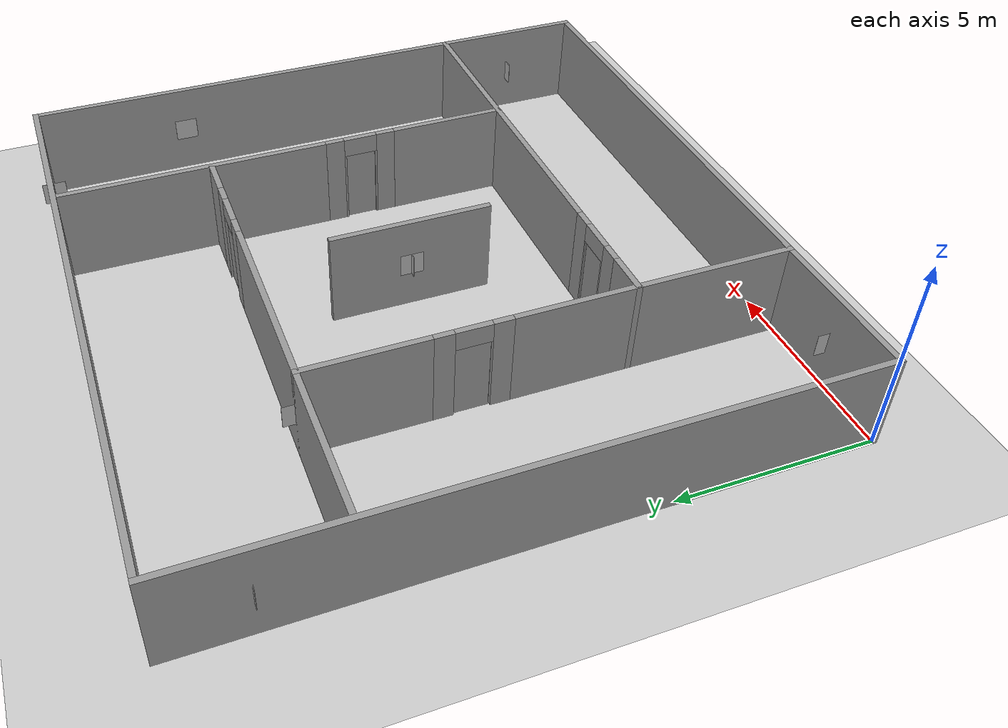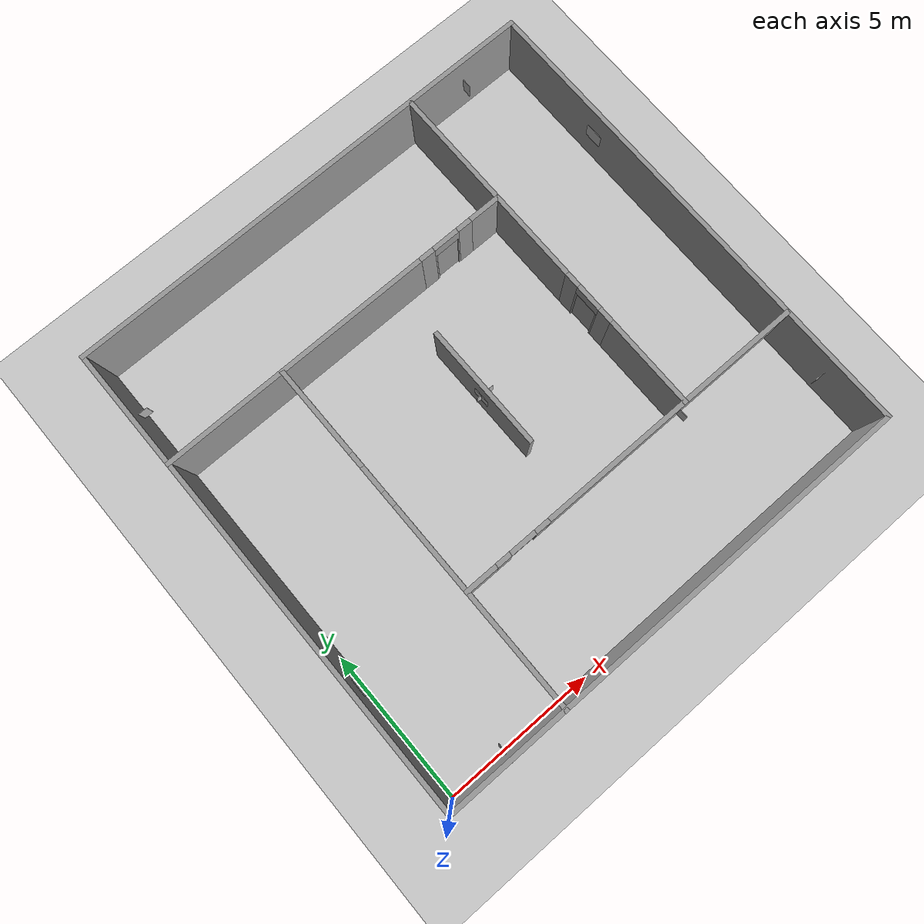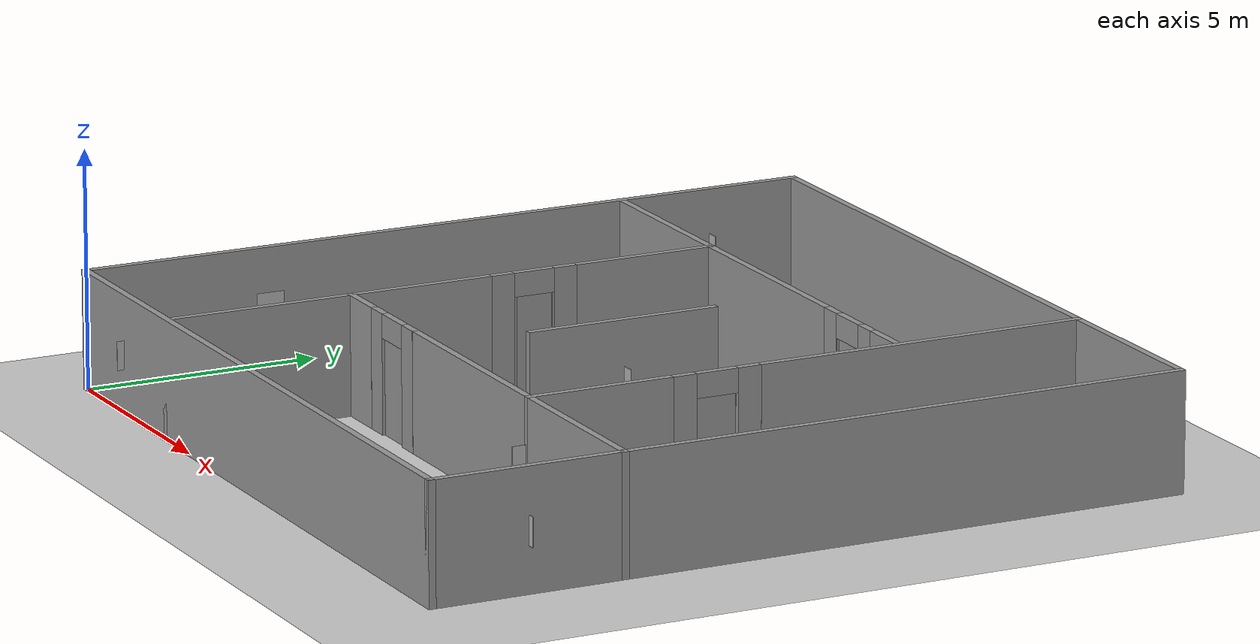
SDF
<sdf version="1.7">
 <world name="default">
  <light name="sun" type="directional">
   <pose>0 0 10 0 -0 0</pose>
   <diffuse>0.8 0.8 0.8 1</diffuse>
   <specular>0.2 0.2 0.2 1</specular>
   <attenuation>
    <range>1000</range>
    <constant>0.9</constant>
    <linear>0.01</linear>
    <quadratic>0.001</quadratic>
   </attenuation>
   <direction>-0.5 0.1 -0.9</direction>
   <spot><inner_angle>0</inner_angle><outer_angle>0</outer_angle><falloff>0</falloff></spot>
  </light>
  <model name="ground_plane">
   <static>1</static>
   <link name="link">
    <collision name="collision">
     <geometry><plane><normal>0 0 1</normal><size>100 100</size></plane></geometry>
     <surface><friction><ode><mu>100</mu><mu2>50</mu2></ode></friction></surface>
    </collision>
    <visual name="visual">
     <cast_shadows>0</cast_shadows>
     <geometry><plane><normal>0 0 1</normal><size>100 100</size></plane></geometry>
     <material>
      <script><uri>file://media/materials/scripts/gazebo.material</uri><name>Gazebo/Grey</name></script>
     </material>
    </visual>
   </link>
  </model>
  <gravity>0 0 -9.8</gravity>
  <magnetic_field>6e-06 2.3e-05 -4.2e-05</magnetic_field>
  <atmosphere type="adiabatic"/>
  <plugin name="ros_interface_plugin" filename="librotors_gazebo_ros_interface_plugin.so"/>
  <physics type="ode">
   <max_step_size>0.001</max_step_size>
   <real_time_factor>1</real_time_factor>
   <real_time_update_rate>1000</real_time_update_rate>
  </physics>
  <scene><ambient>0.4 0.4 0.4 1</ambient><background>0.7 0.7 0.7 1</background><shadows>1</shadows></scene>
  <spherical_coordinates>
   <surface_model>EARTH_WGS84</surface_model>
   <latitude_deg>0</latitude_deg>
   <longitude_deg>0</longitude_deg>
   <elevation>0</elevation>
   <heading_deg>0</heading_deg>
  </spherical_coordinates>
  <model name="room1">
   <pose>8 8 0 0 -0 0</pose>
   <link name="Wall_1">
    <collision name="Wall_1_Collision">
     <geometry><box><size>16.15 0.15 2.5</size></box></geometry>
     <pose>0 0 1.25 0 -0 0</pose>
    </collision>
    <visual name="Wall_1_Visual">
     <pose>0 0 1.25 0 -0 0</pose>
     <geometry><box><size>16.15 0.15 2.5</size></box></geometry>
     <material>
      <script><uri>file://media/materials/scripts/gazebo.material</uri><name>Gazebo/Grey</name></script>
      <ambient>1 1 1 1</ambient>
     </material>
     <meta><layer>0</layer></meta>
    </visual>
    <pose>0 -8 0 0 -0 0</pose>
   </link>
   <link name="Wall_11">
    <pose>-2 4 0 0 -0 0</pose>
    <visual name="Wall_11_Visual_0">
     <pose>-1.5125 0 1.25 0 -0 0</pose>
     <geometry><box><size>9.125 0.15 2.5</size></box></geometry>
     <material>
      <script><uri>file://media/materials/scripts/gazebo.material</uri><name>Gazebo/Grey</name></script>
      <ambient>1 1 1 1</ambient>
     </material>
     <meta><layer>0</layer></meta>
    </visual>
    <collision name="Wall_11_Collision_0">
     <geometry><box><size>9.125 0.15 2.5</size></box></geometry>
     <pose>-1.5125 0 1.25 0 -0 0</pose>
    </collision>
    <visual name="Wall_11_Visual_1">
     <pose>5.5125 0 1.25 0 -0 0</pose>
     <geometry><box><size>1.125 0.15 2.5</size></box></geometry>
     <material>
      <script><uri>file://media/materials/scripts/gazebo.material</uri><name>Gazebo/Grey</name></script>
      <ambient>1 1 1 1</ambient>
     </material>
     <meta><layer>0</layer></meta>
    </visual>
    <collision name="Wall_11_Collision_1">
     <geometry><box><size>1.125 0.15 2.5</size></box></geometry>
     <pose>5.5125 0 1.25 0 -0 0</pose>
    </collision>
   </link>
   <link name="Wall_13">
    <pose>4 2 0 0 -0 -1.5708</pose>
    <visual name="Wall_13_Visual_0">
     <pose>-2.5125 0 1.25 0 -0 0</pose>
     <geometry><box><size>7.125 0.15 2.5</size></box></geometry>
     <material>
      <script><uri>file://media/materials/scripts/gazebo.material</uri><name>Gazebo/Grey</name></script>
      <ambient>1 1 1 1</ambient>
     </material>
     <meta><layer>0</layer></meta>
    </visual>
    <collision name="Wall_13_Collision_0">
     <geometry><box><size>7.125 0.15 2.5</size></box></geometry>
     <pose>-2.5125 0 1.25 0 -0 0</pose>
    </collision>
    <visual name="Wall_13_Visual_1">
     <pose>4.5125 0 1.25 0 -0 0</pose>
     <geometry><box><size>3.125 0.15 2.5</size></box></geometry>
     <material>
      <script><uri>file://media/materials/scripts/gazebo.material</uri><name>Gazebo/Grey</name></script>
      <ambient>1 1 1 1</ambient>
     </material>
     <meta><layer>0</layer></meta>
    </visual>
    <collision name="Wall_13_Collision_1">
     <geometry><box><size>3.125 0.15 2.5</size></box></geometry>
     <pose>4.5125 0 1.25 0 -0 0</pose>
    </collision>
   </link>
   <link name="Wall_15">
    <pose>2 -4 0 0 -0 0</pose>
    <visual name="Wall_15_Visual_0">
     <pose>-5.5125 0 1.25 0 -0 0</pose>
     <geometry><box><size>1.125 0.15 2.5</size></box></geometry>
     <material>
      <script><uri>file://media/materials/scripts/gazebo.material</uri><name>Gazebo/Grey</name></script>
      <ambient>1 1 1 1</ambient>
     </material>
     <meta><layer>0</layer></meta>
    </visual>
    <collision name="Wall_15_Collision_0">
     <geometry><box><size>1.125 0.15 2.5</size></box></geometry>
     <pose>-5.5125 0 1.25 0 -0 0</pose>
    </collision>
    <visual name="Wall_15_Visual_1">
     <pose>1.5125 0 1.25 0 -0 0</pose>
     <geometry><box><size>9.125 0.15 2.5</size></box></geometry>
     <material>
      <script><uri>file://media/materials/scripts/gazebo.material</uri><name>Gazebo/Grey</name></script>
      <ambient>1 1 1 1</ambient>
     </material>
     <meta><layer>0</layer></meta>
    </visual>
    <collision name="Wall_15_Collision_1">
     <geometry><box><size>9.125 0.15 2.5</size></box></geometry>
     <pose>1.5125 0 1.25 0 -0 0</pose>
    </collision>
   </link>
   <link name="Wall_17">
    <collision name="Wall_17_Collision">
     <geometry><box><size>4.15 0.15 2.5</size></box></geometry>
     <pose>0 0 1.25 0 -0 0</pose>
    </collision>
    <visual name="Wall_17_Visual">
     <pose>0 0 1.25 0 -0 0</pose>
     <geometry><box><size>4.15 0.15 2.5</size></box></geometry>
     <material>
      <script><uri>file://media/materials/scripts/gazebo.material</uri><name>Gazebo/Grey</name></script>
      <ambient>1 1 1 1</ambient>
     </material>
     <meta><layer>0</layer></meta>
    </visual>
    <pose>0 0 0 0 -0 1.5708</pose>
   </link>
   <link name="Wall_3">
    <collision name="Wall_3_Collision">
     <geometry><box><size>16.15 0.15 2.5</size></box></geometry>
     <pose>0 0 1.25 0 -0 0</pose>
    </collision>
    <visual name="Wall_3_Visual">
     <pose>0 0 1.25 0 -0 0</pose>
     <geometry><box><size>16.15 0.15 2.5</size></box></geometry>
     <material>
      <script><uri>file://media/materials/scripts/gazebo.material</uri><name>Gazebo/Grey</name></script>
      <ambient>1 1 1 1</ambient>
     </material>
     <meta><layer>0</layer></meta>
    </visual>
    <pose>-8 0 0 0 -0 1.5708</pose>
   </link>
   <link name="Wall_5">
    <collision name="Wall_5_Collision">
     <geometry><box><size>16.15 0.15 2.5</size></box></geometry>
     <pose>0 0 1.25 0 -0 0</pose>
    </collision>
    <visual name="Wall_5_Visual">
     <pose>0 0 1.25 0 -0 0</pose>
     <geometry><box><size>16.15 0.15 2.5</size></box></geometry>
     <material>
      <script><uri>file://media/materials/scripts/gazebo.material</uri><name>Gazebo/Grey</name></script>
      <ambient>1 1 1 1</ambient>
     </material>
     <meta><layer>0</layer></meta>
    </visual>
    <pose>0 8 0 0 -0 0</pose>
   </link>
   <link name="Wall_7">
    <collision name="Wall_7_Collision">
     <geometry><box><size>16.15 0.15 2.5</size></box></geometry>
     <pose>0 0 1.25 0 -0 0</pose>
    </collision>
    <visual name="Wall_7_Visual">
     <pose>0 0 1.25 0 -0 0</pose>
     <geometry><box><size>16.15 0.15 2.5</size></box></geometry>
     <material>
      <script><uri>file://media/materials/scripts/gazebo.material</uri><name>Gazebo/Grey</name></script>
      <ambient>1 1 1 1</ambient>
     </material>
     <meta><layer>0</layer></meta>
    </visual>
    <pose>8 0 0 0 -0 -1.5708</pose>
   </link>
   <link name="Wall_9">
    <pose>-4 -2 0 0 -0 1.5708</pose>
    <visual name="Wall_9_Visual_0">
     <pose>-2.5125 0 1.25 0 -0 0</pose>
     <geometry><box><size>7.125 0.15 2.5</size></box></geometry>
     <material>
      <script><uri>file://media/materials/scripts/gazebo.material</uri><name>Gazebo/Grey</name></script>
      <ambient>1 1 1 1</ambient>
     </material>
     <meta><layer>0</layer></meta>
    </visual>
    <collision name="Wall_9_Collision_0">
     <geometry><box><size>7.125 0.15 2.5</size></box></geometry>
     <pose>-2.5125 0 1.25 0 -0 0</pose>
    </collision>
    <visual name="Wall_9_Visual_1">
     <pose>4.5125 0 1.25 0 -0 0</pose>
     <geometry><box><size>3.125 0.15 2.5</size></box></geometry>
     <material>
      <script><uri>file://media/materials/scripts/gazebo.material</uri><name>Gazebo/Grey</name></script>
      <ambient>1 1 1 1</ambient>
     </material>
     <meta><layer>0</layer></meta>
    </visual>
    <collision name="Wall_9_Collision_1">
     <geometry><box><size>3.125 0.15 2.5</size></box></geometry>
     <pose>4.5125 0 1.25 0 -0 0</pose>
    </collision>
   </link>
   <static>1</static>
  </model>
  <model name="wall_with_door_no_gap">
   <link name="Wall">
    <pose>0 0 0 0 -4e-06 0</pose>
    <inertial>
     <inertia><ixx>1</ixx><ixy>0</ixy><ixz>0</ixz><iyy>1</iyy><iyz>0</iyz><izz>1</izz></inertia>
     <mass>1</mass>
    </inertial>
    <visual name="Wall_Visual_4">
     <pose>0.425 -0.055 1 0 -0 0</pose>
     <geometry><box><size>0.05 0.04 2</size></box></geometry>
     <material>
      <script><uri>file://media/materials/scripts/gazebo.material</uri><name>Gazebo/Grey</name></script>
      <ambient>1 1 1 1</ambient>
      <shader type="pixel"><normal_map>__default__</normal_map></shader>
      <emissive>0 0 0 1</emissive>
      <diffuse>0.7 0.7 0.7 1</diffuse>
      <specular>0.01 0.01 0.01 1</specular>
     </material>
     <meta><layer>0</layer></meta>
    </visual>
    <visual name="Wall_Visual_0">
     <pose>-0.7 0 1.25 0 -0 0</pose>
     <geometry><box><size>0.5 0.15 2.5</size></box></geometry>
     <material>
      <script><uri>file://media/materials/scripts/gazebo.material</uri><name>Gazebo/Grey</name></script>
      <ambient>1 1 1 1</ambient>
      <shader type="pixel"><normal_map>__default__</normal_map></shader>
      <emissive>0 0 0 1</emissive>
      <diffuse>0.7 0.7 0.7 1</diffuse>
      <specular>0.01 0.01 0.01 1</specular>
     </material>
     <meta><layer>0</layer></meta>
    </visual>
    <visual name="Wall_visual_3">
     <pose>-0.425 -0.055 1 0 -0 0</pose>
     <geometry><box><size>0.05 0.04 2</size></box></geometry>
     <material>
      <script><uri>file://media/materials/scripts/gazebo.material</uri><name>Gazebo/Grey</name></script>
      <ambient>1 1 1 1</ambient>
      <shader type="pixel"><normal_map>__default__</normal_map></shader>
      <emissive>0 0 0 1</emissive>
      <diffuse>0.7 0.7 0.7 1</diffuse>
      <specular>0.01 0.01 0.01 1</specular>
     </material>
     <meta><layer>0</layer></meta>
    </visual>
    <visual name="Wall_Visual_1">
     <pose>0.7 0 1.25 0 -0 0</pose>
     <geometry><box><size>0.5 0.15 2.5</size></box></geometry>
     <material>
      <script><uri>file://media/materials/scripts/gazebo.material</uri><name>Gazebo/Grey</name></script>
      <ambient>1 1 1 1</ambient>
      <shader type="pixel"><normal_map>__default__</normal_map></shader>
      <emissive>0 0 0 1</emissive>
      <diffuse>0.7 0.7 0.7 1</diffuse>
      <specular>0.01 0.01 0.01 1</specular>
     </material>
     <meta><layer>0</layer></meta>
    </visual>
    <visual name="Wall_Visual_2">
     <pose>0 0 2.25 0 -0 0</pose>
     <geometry><box><size>0.9 0.15 0.5</size></box></geometry>
     <material>
      <script><uri>file://media/materials/scripts/gazebo.material</uri><name>Gazebo/Grey</name></script>
      <ambient>1 1 1 1</ambient>
      <shader type="pixel"><normal_map>__default__</normal_map></shader>
      <emissive>0 0 0 1</emissive>
      <diffuse>0.7 0.7 0.7 1</diffuse>
      <specular>0.01 0.01 0.01 1</specular>
     </material>
     <meta><layer>0</layer></meta>
    </visual>
    <collision name="Wall_Collision_3">
     <pose>-0.425 -0.055 1 0 -0 0</pose>
     <geometry><box><size>0.05 0.04 2</size></box></geometry>
     <surface>
      <friction>
       <ode><mu>1</mu><mu2>1</mu2><fdir1>0 0 0</fdir1><slip1>0</slip1><slip2>0</slip2></ode>
       <torsional>
        <coefficient>1</coefficient>
        <patch_radius>0</patch_radius>
        <surface_radius>0</surface_radius>
        <use_patch_radius>1</use_patch_radius>
        <ode><slip>0</slip></ode>
       </torsional>
      </friction>
      <bounce><restitution_coefficient>0</restitution_coefficient><threshold>1e+06</threshold></bounce>
      <contact>
       <collide_without_contact>0</collide_without_contact>
       <collide_without_contact_bitmask>1</collide_without_contact_bitmask>
       <collide_bitmask>1</collide_bitmask>
       <ode>
        <soft_cfm>0</soft_cfm>
        <soft_erp>0.2</soft_erp>
        <kp>1e+13</kp>
        <kd>1</kd>
        <max_vel>0.01</max_vel>
        <min_depth>0</min_depth>
       </ode>
       <bullet>
        <split_impulse>1</split_impulse>
        <split_impulse_penetration_threshold>-0.01</split_impulse_penetration_threshold>
        <soft_cfm>0</soft_cfm>
        <soft_erp>0.2</soft_erp>
        <kp>1e+13</kp>
        <kd>1</kd>
       </bullet>
      </contact>
     </surface>
    </collision>
    <collision name="Wall_Collision_4">
     <pose>0.425 -0.055 1 0 -0 0</pose>
     <geometry><box><size>0.05 0.04 2</size></box></geometry>
     <surface>
      <friction>
       <ode><mu>1</mu><mu2>1</mu2><fdir1>0 0 0</fdir1><slip1>0</slip1><slip2>0</slip2></ode>
       <torsional>
        <coefficient>1</coefficient>
        <patch_radius>0</patch_radius>
        <surface_radius>0</surface_radius>
        <use_patch_radius>1</use_patch_radius>
        <ode><slip>0</slip></ode>
       </torsional>
      </friction>
      <bounce><restitution_coefficient>0</restitution_coefficient><threshold>1e+06</threshold></bounce>
      <contact>
       <collide_without_contact>0</collide_without_contact>
       <collide_without_contact_bitmask>1</collide_without_contact_bitmask>
       <collide_bitmask>1</collide_bitmask>
       <ode>
        <soft_cfm>0</soft_cfm>
        <soft_erp>0.2</soft_erp>
        <kp>1e+13</kp>
        <kd>1</kd>
        <max_vel>0.01</max_vel>
        <min_depth>0</min_depth>
       </ode>
       <bullet>
        <split_impulse>1</split_impulse>
        <split_impulse_penetration_threshold>-0.01</split_impulse_penetration_threshold>
        <soft_cfm>0</soft_cfm>
        <soft_erp>0.2</soft_erp>
        <kp>1e+13</kp>
        <kd>1</kd>
       </bullet>
      </contact>
     </surface>
    </collision>
    <collision name="Wall_Collision_1">
     <pose>0.7 0 1.25 0 -0 0</pose>
     <geometry><box><size>0.5 0.15 2.5</size></box></geometry>
     <surface>
      <friction>
       <ode><mu>1</mu><mu2>1</mu2><fdir1>0 0 0</fdir1><slip1>0</slip1><slip2>0</slip2></ode>
       <torsional>
        <coefficient>1</coefficient>
        <patch_radius>0</patch_radius>
        <surface_radius>0</surface_radius>
        <use_patch_radius>1</use_patch_radius>
        <ode><slip>0</slip></ode>
       </torsional>
      </friction>
      <bounce><restitution_coefficient>0</restitution_coefficient><threshold>1e+06</threshold></bounce>
      <contact>
       <collide_without_contact>0</collide_without_contact>
       <collide_without_contact_bitmask>1</collide_without_contact_bitmask>
       <collide_bitmask>1</collide_bitmask>
       <ode>
        <soft_cfm>0</soft_cfm>
        <soft_erp>0.2</soft_erp>
        <kp>1e+13</kp>
        <kd>1</kd>
        <max_vel>0.01</max_vel>
        <min_depth>0</min_depth>
       </ode>
       <bullet>
        <split_impulse>1</split_impulse>
        <split_impulse_penetration_threshold>-0.01</split_impulse_penetration_threshold>
        <soft_cfm>0</soft_cfm>
        <soft_erp>0.2</soft_erp>
        <kp>1e+13</kp>
        <kd>1</kd>
       </bullet>
      </contact>
     </surface>
    </collision>
    <collision name="Wall_Collision_0">
     <pose>-0.7 0 1.25 0 -0 0</pose>
     <geometry><box><size>0.5 0.15 2.5</size></box></geometry>
     <surface>
      <friction>
       <ode><mu>1</mu><mu2>1</mu2><fdir1>0 0 0</fdir1><slip1>0</slip1><slip2>0</slip2></ode>
       <torsional>
        <coefficient>1</coefficient>
        <patch_radius>0</patch_radius>
        <surface_radius>0</surface_radius>
        <use_patch_radius>1</use_patch_radius>
        <ode><slip>0</slip></ode>
       </torsional>
      </friction>
      <bounce><restitution_coefficient>0</restitution_coefficient><threshold>1e+06</threshold></bounce>
      <contact>
       <collide_without_contact>0</collide_without_contact>
       <collide_without_contact_bitmask>1</collide_without_contact_bitmask>
       <collide_bitmask>1</collide_bitmask>
       <ode>
        <soft_cfm>0</soft_cfm>
        <soft_erp>0.2</soft_erp>
        <kp>1e+13</kp>
        <kd>1</kd>
        <max_vel>0.01</max_vel>
        <min_depth>0</min_depth>
       </ode>
       <bullet>
        <split_impulse>1</split_impulse>
        <split_impulse_penetration_threshold>-0.01</split_impulse_penetration_threshold>
        <soft_cfm>0</soft_cfm>
        <soft_erp>0.2</soft_erp>
        <kp>1e+13</kp>
        <kd>1</kd>
       </bullet>
      </contact>
     </surface>
    </collision>
    <collision name="Wall_Collision_2">
     <pose>0 0 2.25 0 -0 0</pose>
     <geometry><box><size>0.9 0.15 0.5</size></box></geometry>
     <surface>
      <friction>
       <ode><mu>1</mu><mu2>1</mu2><fdir1>0 0 0</fdir1><slip1>0</slip1><slip2>0</slip2></ode>
       <torsional>
        <coefficient>1</coefficient>
        <patch_radius>0</patch_radius>
        <surface_radius>0</surface_radius>
        <use_patch_radius>1</use_patch_radius>
        <ode><slip>0</slip></ode>
       </torsional>
      </friction>
      <bounce><restitution_coefficient>0</restitution_coefficient><threshold>1e+06</threshold></bounce>
      <contact>
       <collide_without_contact>0</collide_without_contact>
       <collide_without_contact_bitmask>1</collide_without_contact_bitmask>
       <collide_bitmask>1</collide_bitmask>
       <ode>
        <soft_cfm>0</soft_cfm>
        <soft_erp>0.2</soft_erp>
        <kp>1e+13</kp>
        <kd>1</kd>
        <max_vel>0.01</max_vel>
        <min_depth>0</min_depth>
       </ode>
       <bullet>
        <split_impulse>1</split_impulse>
        <split_impulse_penetration_threshold>-0.01</split_impulse_penetration_threshold>
        <soft_cfm>0</soft_cfm>
        <soft_erp>0.2</soft_erp>
        <kp>1e+13</kp>
        <kd>1</kd>
       </bullet>
      </contact>
     </surface>
    </collision>
    <static>1</static>
   </link>
   <link name="door">
    <inertial>
     <mass>1</mass>
     <inertia>
      <ixx>0.166667</ixx>
      <ixy>0</ixy>
      <ixz>0</ixz>
      <iyy>0.166667</iyy>
      <iyz>0</iyz>
      <izz>0.166667</izz>
     </inertia>
    </inertial>
    <pose>-0 -0 1 0 -4e-06 0</pose>
    <visual name="visual">
     <pose>0.01 0 0 0 -0 0</pose>
     <geometry><box><size>0.86 0.04 2</size></box></geometry>
     <material>
      <lighting>1</lighting>
      <script><uri>file://media/materials/scripts/gazebo.material</uri><name>Gazebo/Grey</name></script>
      <shader type="pixel"><normal_map>__default__</normal_map></shader>
      <ambient>0.3 0.3 0.3 1</ambient>
      <diffuse>0.7 0.7 0.7 1</diffuse>
      <specular>0.01 0.01 0.01 1</specular>
      <emissive>0 0 0 1</emissive>
     </material>
    </visual>
    <collision name="collision">
     <pose>0.01 0 0 0 -0 0</pose>
     <geometry><box><size>0.84 0.04 2</size></box></geometry>
     <surface>
      <friction>
       <ode><mu>1</mu><mu2>1</mu2><fdir1>0 0 0</fdir1><slip1>0</slip1><slip2>0</slip2></ode>
       <torsional>
        <coefficient>1</coefficient>
        <patch_radius>0</patch_radius>
        <surface_radius>0</surface_radius>
        <use_patch_radius>1</use_patch_radius>
        <ode><slip>0</slip></ode>
       </torsional>
      </friction>
      <bounce><restitution_coefficient>0</restitution_coefficient><threshold>1e+06</threshold></bounce>
      <contact>
       <collide_without_contact>0</collide_without_contact>
       <collide_without_contact_bitmask>1</collide_without_contact_bitmask>
       <collide_bitmask>1</collide_bitmask>
       <ode>
        <soft_cfm>0</soft_cfm>
        <soft_erp>0.2</soft_erp>
        <kp>1e+13</kp>
        <kd>1</kd>
        <max_vel>0.01</max_vel>
        <min_depth>0</min_depth>
       </ode>
       <bullet>
        <split_impulse>1</split_impulse>
        <split_impulse_penetration_threshold>-0.01</split_impulse_penetration_threshold>
        <soft_cfm>0</soft_cfm>
        <soft_erp>0.2</soft_erp>
        <kp>1e+13</kp>
        <kd>1</kd>
       </bullet>
      </contact>
     </surface>
    </collision>
    <static>0</static>
   </link>
   <joint name="Door_JOINT" type="revolute">
    <parent>Wall</parent>
    <child>door</child>
    <pose>-0.43 0 0 0 -0 0</pose>
    <axis>
     <xyz>0 0 1</xyz>
     <limit><lower>0</lower><upper>1.57</upper><effort>-1</effort><velocity>-1</velocity></limit>
     <dynamics>
      <spring_reference>0</spring_reference>
      <spring_stiffness>0</spring_stiffness>
      <damping>0</damping>
      <friction>0</friction>
     </dynamics>
    </axis>
    <physics>
     <ode><limit><cfm>0</cfm><erp>0.2</erp></limit><suspension><cfm>0</cfm><erp>0.2</erp></suspension></ode>
    </physics>
   </joint>
   <joint name="WALL_FIXED" type="fixed"><parent>world</parent><child>Wall</child></joint>
   <plugin name="wall_and_door_plugin" filename="libDoorControlPlugin.so">
    <initial_position>1.57</initial_position>
    <switch_flag>true</switch_flag>
    <switch_duration>20</switch_duration>
   </plugin>
   <static>0</static>
   <pose>4.0002 8 0 1e-06 4e-06 1.5708</pose>
  </model>
  <model name="wall_with_door_no_gap_0">
   <link name="Wall">
    <pose>0 0 0 0 -4e-06 0</pose>
    <inertial>
     <inertia><ixx>1</ixx><ixy>0</ixy><ixz>0</ixz><iyy>1</iyy><iyz>0</iyz><izz>1</izz></inertia>
     <mass>1</mass>
    </inertial>
    <visual name="Wall_Visual_4">
     <pose>0.425 -0.055 1 0 -0 0</pose>
     <geometry><box><size>0.05 0.04 2</size></box></geometry>
     <material>
      <script><uri>file://media/materials/scripts/gazebo.material</uri><name>Gazebo/Grey</name></script>
      <ambient>1 1 1 1</ambient>
      <shader type="pixel"><normal_map>__default__</normal_map></shader>
      <emissive>0 0 0 1</emissive>
      <diffuse>0.7 0.7 0.7 1</diffuse>
      <specular>0.01 0.01 0.01 1</specular>
     </material>
     <meta><layer>0</layer></meta>
    </visual>
    <visual name="Wall_Visual_0">
     <pose>-0.7 0 1.25 0 -0 0</pose>
     <geometry><box><size>0.5 0.15 2.5</size></box></geometry>
     <material>
      <script><uri>file://media/materials/scripts/gazebo.material</uri><name>Gazebo/Grey</name></script>
      <ambient>1 1 1 1</ambient>
      <shader type="pixel"><normal_map>__default__</normal_map></shader>
      <emissive>0 0 0 1</emissive>
      <diffuse>0.7 0.7 0.7 1</diffuse>
      <specular>0.01 0.01 0.01 1</specular>
     </material>
     <meta><layer>0</layer></meta>
    </visual>
    <visual name="Wall_visual_3">
     <pose>-0.425 -0.055 1 0 -0 0</pose>
     <geometry><box><size>0.05 0.04 2</size></box></geometry>
     <material>
      <script><uri>file://media/materials/scripts/gazebo.material</uri><name>Gazebo/Grey</name></script>
      <ambient>1 1 1 1</ambient>
      <shader type="pixel"><normal_map>__default__</normal_map></shader>
      <emissive>0 0 0 1</emissive>
      <diffuse>0.7 0.7 0.7 1</diffuse>
      <specular>0.01 0.01 0.01 1</specular>
     </material>
     <meta><layer>0</layer></meta>
    </visual>
    <visual name="Wall_Visual_1">
     <pose>0.7 0 1.25 0 -0 0</pose>
     <geometry><box><size>0.5 0.15 2.5</size></box></geometry>
     <material>
      <script><uri>file://media/materials/scripts/gazebo.material</uri><name>Gazebo/Grey</name></script>
      <ambient>1 1 1 1</ambient>
      <shader type="pixel"><normal_map>__default__</normal_map></shader>
      <emissive>0 0 0 1</emissive>
      <diffuse>0.7 0.7 0.7 1</diffuse>
      <specular>0.01 0.01 0.01 1</specular>
     </material>
     <meta><layer>0</layer></meta>
    </visual>
    <visual name="Wall_Visual_2">
     <pose>0 0 2.25 0 -0 0</pose>
     <geometry><box><size>0.9 0.15 0.5</size></box></geometry>
     <material>
      <script><uri>file://media/materials/scripts/gazebo.material</uri><name>Gazebo/Grey</name></script>
      <ambient>1 1 1 1</ambient>
      <shader type="pixel"><normal_map>__default__</normal_map></shader>
      <emissive>0 0 0 1</emissive>
      <diffuse>0.7 0.7 0.7 1</diffuse>
      <specular>0.01 0.01 0.01 1</specular>
     </material>
     <meta><layer>0</layer></meta>
    </visual>
    <collision name="Wall_Collision_3">
     <pose>-0.425 -0.055 1 0 -0 0</pose>
     <geometry><box><size>0.05 0.04 2</size></box></geometry>
     <surface>
      <friction>
       <ode><mu>1</mu><mu2>1</mu2><fdir1>0 0 0</fdir1><slip1>0</slip1><slip2>0</slip2></ode>
       <torsional>
        <coefficient>1</coefficient>
        <patch_radius>0</patch_radius>
        <surface_radius>0</surface_radius>
        <use_patch_radius>1</use_patch_radius>
        <ode><slip>0</slip></ode>
       </torsional>
      </friction>
      <bounce><restitution_coefficient>0</restitution_coefficient><threshold>1e+06</threshold></bounce>
      <contact>
       <collide_without_contact>0</collide_without_contact>
       <collide_without_contact_bitmask>1</collide_without_contact_bitmask>
       <collide_bitmask>1</collide_bitmask>
       <ode>
        <soft_cfm>0</soft_cfm>
        <soft_erp>0.2</soft_erp>
        <kp>1e+13</kp>
        <kd>1</kd>
        <max_vel>0.01</max_vel>
        <min_depth>0</min_depth>
       </ode>
       <bullet>
        <split_impulse>1</split_impulse>
        <split_impulse_penetration_threshold>-0.01</split_impulse_penetration_threshold>
        <soft_cfm>0</soft_cfm>
        <soft_erp>0.2</soft_erp>
        <kp>1e+13</kp>
        <kd>1</kd>
       </bullet>
      </contact>
     </surface>
    </collision>
    <collision name="Wall_Collision_4">
     <pose>0.425 -0.055 1 0 -0 0</pose>
     <geometry><box><size>0.05 0.04 2</size></box></geometry>
     <surface>
      <friction>
       <ode><mu>1</mu><mu2>1</mu2><fdir1>0 0 0</fdir1><slip1>0</slip1><slip2>0</slip2></ode>
       <torsional>
        <coefficient>1</coefficient>
        <patch_radius>0</patch_radius>
        <surface_radius>0</surface_radius>
        <use_patch_radius>1</use_patch_radius>
        <ode><slip>0</slip></ode>
       </torsional>
      </friction>
      <bounce><restitution_coefficient>0</restitution_coefficient><threshold>1e+06</threshold></bounce>
      <contact>
       <collide_without_contact>0</collide_without_contact>
       <collide_without_contact_bitmask>1</collide_without_contact_bitmask>
       <collide_bitmask>1</collide_bitmask>
       <ode>
        <soft_cfm>0</soft_cfm>
        <soft_erp>0.2</soft_erp>
        <kp>1e+13</kp>
        <kd>1</kd>
        <max_vel>0.01</max_vel>
        <min_depth>0</min_depth>
       </ode>
       <bullet>
        <split_impulse>1</split_impulse>
        <split_impulse_penetration_threshold>-0.01</split_impulse_penetration_threshold>
        <soft_cfm>0</soft_cfm>
        <soft_erp>0.2</soft_erp>
        <kp>1e+13</kp>
        <kd>1</kd>
       </bullet>
      </contact>
     </surface>
    </collision>
    <collision name="Wall_Collision_1">
     <pose>0.7 0 1.25 0 -0 0</pose>
     <geometry><box><size>0.5 0.15 2.5</size></box></geometry>
     <surface>
      <friction>
       <ode><mu>1</mu><mu2>1</mu2><fdir1>0 0 0</fdir1><slip1>0</slip1><slip2>0</slip2></ode>
       <torsional>
        <coefficient>1</coefficient>
        <patch_radius>0</patch_radius>
        <surface_radius>0</surface_radius>
        <use_patch_radius>1</use_patch_radius>
        <ode><slip>0</slip></ode>
       </torsional>
      </friction>
      <bounce><restitution_coefficient>0</restitution_coefficient><threshold>1e+06</threshold></bounce>
      <contact>
       <collide_without_contact>0</collide_without_contact>
       <collide_without_contact_bitmask>1</collide_without_contact_bitmask>
       <collide_bitmask>1</collide_bitmask>
       <ode>
        <soft_cfm>0</soft_cfm>
        <soft_erp>0.2</soft_erp>
        <kp>1e+13</kp>
        <kd>1</kd>
        <max_vel>0.01</max_vel>
        <min_depth>0</min_depth>
       </ode>
       <bullet>
        <split_impulse>1</split_impulse>
        <split_impulse_penetration_threshold>-0.01</split_impulse_penetration_threshold>
        <soft_cfm>0</soft_cfm>
        <soft_erp>0.2</soft_erp>
        <kp>1e+13</kp>
        <kd>1</kd>
       </bullet>
      </contact>
     </surface>
    </collision>
    <collision name="Wall_Collision_0">
     <pose>-0.7 0 1.25 0 -0 0</pose>
     <geometry><box><size>0.5 0.15 2.5</size></box></geometry>
     <surface>
      <friction>
       <ode><mu>1</mu><mu2>1</mu2><fdir1>0 0 0</fdir1><slip1>0</slip1><slip2>0</slip2></ode>
       <torsional>
        <coefficient>1</coefficient>
        <patch_radius>0</patch_radius>
        <surface_radius>0</surface_radius>
        <use_patch_radius>1</use_patch_radius>
        <ode><slip>0</slip></ode>
       </torsional>
      </friction>
      <bounce><restitution_coefficient>0</restitution_coefficient><threshold>1e+06</threshold></bounce>
      <contact>
       <collide_without_contact>0</collide_without_contact>
       <collide_without_contact_bitmask>1</collide_without_contact_bitmask>
       <collide_bitmask>1</collide_bitmask>
       <ode>
        <soft_cfm>0</soft_cfm>
        <soft_erp>0.2</soft_erp>
        <kp>1e+13</kp>
        <kd>1</kd>
        <max_vel>0.01</max_vel>
        <min_depth>0</min_depth>
       </ode>
       <bullet>
        <split_impulse>1</split_impulse>
        <split_impulse_penetration_threshold>-0.01</split_impulse_penetration_threshold>
        <soft_cfm>0</soft_cfm>
        <soft_erp>0.2</soft_erp>
        <kp>1e+13</kp>
        <kd>1</kd>
       </bullet>
      </contact>
     </surface>
    </collision>
    <collision name="Wall_Collision_2">
     <pose>0 0 2.25 0 -0 0</pose>
     <geometry><box><size>0.9 0.15 0.5</size></box></geometry>
     <surface>
      <friction>
       <ode><mu>1</mu><mu2>1</mu2><fdir1>0 0 0</fdir1><slip1>0</slip1><slip2>0</slip2></ode>
       <torsional>
        <coefficient>1</coefficient>
        <patch_radius>0</patch_radius>
        <surface_radius>0</surface_radius>
        <use_patch_radius>1</use_patch_radius>
        <ode><slip>0</slip></ode>
       </torsional>
      </friction>
      <bounce><restitution_coefficient>0</restitution_coefficient><threshold>1e+06</threshold></bounce>
      <contact>
       <collide_without_contact>0</collide_without_contact>
       <collide_without_contact_bitmask>1</collide_without_contact_bitmask>
       <collide_bitmask>1</collide_bitmask>
       <ode>
        <soft_cfm>0</soft_cfm>
        <soft_erp>0.2</soft_erp>
        <kp>1e+13</kp>
        <kd>1</kd>
        <max_vel>0.01</max_vel>
        <min_depth>0</min_depth>
       </ode>
       <bullet>
        <split_impulse>1</split_impulse>
        <split_impulse_penetration_threshold>-0.01</split_impulse_penetration_threshold>
        <soft_cfm>0</soft_cfm>
        <soft_erp>0.2</soft_erp>
        <kp>1e+13</kp>
        <kd>1</kd>
       </bullet>
      </contact>
     </surface>
    </collision>
    <static>1</static>
   </link>
   <link name="door">
    <inertial>
     <mass>1</mass>
     <inertia>
      <ixx>0.166667</ixx>
      <ixy>0</ixy>
      <ixz>0</ixz>
      <iyy>0.166667</iyy>
      <iyz>0</iyz>
      <izz>0.166667</izz>
     </inertia>
    </inertial>
    <pose>-0 -0 1 0 -4e-06 0</pose>
    <visual name="visual">
     <pose>0.01 0 0 0 -0 0</pose>
     <geometry><box><size>0.86 0.04 2</size></box></geometry>
     <material>
      <lighting>1</lighting>
      <script><uri>file://media/materials/scripts/gazebo.material</uri><name>Gazebo/Grey</name></script>
      <shader type="pixel"><normal_map>__default__</normal_map></shader>
      <ambient>0.3 0.3 0.3 1</ambient>
      <diffuse>0.7 0.7 0.7 1</diffuse>
      <specular>0.01 0.01 0.01 1</specular>
      <emissive>0 0 0 1</emissive>
     </material>
    </visual>
    <collision name="collision">
     <pose>0.01 0 0 0 -0 0</pose>
     <geometry><box><size>0.84 0.04 2</size></box></geometry>
     <surface>
      <friction>
       <ode><mu>1</mu><mu2>1</mu2><fdir1>0 0 0</fdir1><slip1>0</slip1><slip2>0</slip2></ode>
       <torsional>
        <coefficient>1</coefficient>
        <patch_radius>0</patch_radius>
        <surface_radius>0</surface_radius>
        <use_patch_radius>1</use_patch_radius>
        <ode><slip>0</slip></ode>
       </torsional>
      </friction>
      <bounce><restitution_coefficient>0</restitution_coefficient><threshold>1e+06</threshold></bounce>
      <contact>
       <collide_without_contact>0</collide_without_contact>
       <collide_without_contact_bitmask>1</collide_without_contact_bitmask>
       <collide_bitmask>1</collide_bitmask>
       <ode>
        <soft_cfm>0</soft_cfm>
        <soft_erp>0.2</soft_erp>
        <kp>1e+13</kp>
        <kd>1</kd>
        <max_vel>0.01</max_vel>
        <min_depth>0</min_depth>
       </ode>
       <bullet>
        <split_impulse>1</split_impulse>
        <split_impulse_penetration_threshold>-0.01</split_impulse_penetration_threshold>
        <soft_cfm>0</soft_cfm>
        <soft_erp>0.2</soft_erp>
        <kp>1e+13</kp>
        <kd>1</kd>
       </bullet>
      </contact>
     </surface>
    </collision>
    <static>0</static>
   </link>
   <joint name="Door_JOINT" type="revolute">
    <parent>Wall</parent>
    <child>door</child>
    <pose>-0.43 0 0 0 -0 0</pose>
    <axis>
     <xyz>0 0 1</xyz>
     <limit><lower>0</lower><upper>1.57</upper><effort>-1</effort><velocity>-1</velocity></limit>
     <dynamics>
      <spring_reference>0</spring_reference>
      <spring_stiffness>0</spring_stiffness>
      <damping>0</damping>
      <friction>0</friction>
     </dynamics>
    </axis>
    <physics>
     <ode><limit><cfm>0</cfm><erp>0.2</erp></limit><suspension><cfm>0</cfm><erp>0.2</erp></suspension></ode>
    </physics>
   </joint>
   <joint name="WALL_FIXED" type="fixed"><parent>world</parent><child>Wall</child></joint>
   <plugin name="wall_and_door_plugin" filename="libDoorControlPlugin.so">
    <initial_position>1.57</initial_position>
    <switch_flag>true</switch_flag>
    <switch_duration>25</switch_duration>
   </plugin>
   <static>0</static>
   <pose>6 4 0 0 -0 3.14</pose>
  </model>
  <model name="wall_with_door_no_gap_1">
   <link name="Wall">
    <pose>0 0 0 0 -4e-06 0</pose>
    <inertial>
     <inertia><ixx>1</ixx><ixy>0</ixy><ixz>0</ixz><iyy>1</iyy><iyz>0</iyz><izz>1</izz></inertia>
     <mass>1</mass>
    </inertial>
    <visual name="Wall_Visual_4">
     <pose>0.425 -0.055 1 0 -0 0</pose>
     <geometry><box><size>0.05 0.04 2</size></box></geometry>
     <material>
      <script><uri>file://media/materials/scripts/gazebo.material</uri><name>Gazebo/Grey</name></script>
      <ambient>1 1 1 1</ambient>
      <shader type="pixel"><normal_map>__default__</normal_map></shader>
      <emissive>0 0 0 1</emissive>
      <diffuse>0.7 0.7 0.7 1</diffuse>
      <specular>0.01 0.01 0.01 1</specular>
     </material>
     <meta><layer>0</layer></meta>
    </visual>
    <visual name="Wall_Visual_0">
     <pose>-0.7 0 1.25 0 -0 0</pose>
     <geometry><box><size>0.5 0.15 2.5</size></box></geometry>
     <material>
      <script><uri>file://media/materials/scripts/gazebo.material</uri><name>Gazebo/Grey</name></script>
      <ambient>1 1 1 1</ambient>
      <shader type="pixel"><normal_map>__default__</normal_map></shader>
      <emissive>0 0 0 1</emissive>
      <diffuse>0.7 0.7 0.7 1</diffuse>
      <specular>0.01 0.01 0.01 1</specular>
     </material>
     <meta><layer>0</layer></meta>
    </visual>
    <visual name="Wall_visual_3">
     <pose>-0.425 -0.055 1 0 -0 0</pose>
     <geometry><box><size>0.05 0.04 2</size></box></geometry>
     <material>
      <script><uri>file://media/materials/scripts/gazebo.material</uri><name>Gazebo/Grey</name></script>
      <ambient>1 1 1 1</ambient>
      <shader type="pixel"><normal_map>__default__</normal_map></shader>
      <emissive>0 0 0 1</emissive>
      <diffuse>0.7 0.7 0.7 1</diffuse>
      <specular>0.01 0.01 0.01 1</specular>
     </material>
     <meta><layer>0</layer></meta>
    </visual>
    <visual name="Wall_Visual_1">
     <pose>0.7 0 1.25 0 -0 0</pose>
     <geometry><box><size>0.5 0.15 2.5</size></box></geometry>
     <material>
      <script><uri>file://media/materials/scripts/gazebo.material</uri><name>Gazebo/Grey</name></script>
      <ambient>1 1 1 1</ambient>
      <shader type="pixel"><normal_map>__default__</normal_map></shader>
      <emissive>0 0 0 1</emissive>
      <diffuse>0.7 0.7 0.7 1</diffuse>
      <specular>0.01 0.01 0.01 1</specular>
     </material>
     <meta><layer>0</layer></meta>
    </visual>
    <visual name="Wall_Visual_2">
     <pose>0 0 2.25 0 -0 0</pose>
     <geometry><box><size>0.9 0.15 0.5</size></box></geometry>
     <material>
      <script><uri>file://media/materials/scripts/gazebo.material</uri><name>Gazebo/Grey</name></script>
      <ambient>1 1 1 1</ambient>
      <shader type="pixel"><normal_map>__default__</normal_map></shader>
      <emissive>0 0 0 1</emissive>
      <diffuse>0.7 0.7 0.7 1</diffuse>
      <specular>0.01 0.01 0.01 1</specular>
     </material>
     <meta><layer>0</layer></meta>
    </visual>
    <collision name="Wall_Collision_3">
     <pose>-0.425 -0.055 1 0 -0 0</pose>
     <geometry><box><size>0.05 0.04 2</size></box></geometry>
     <surface>
      <friction>
       <ode><mu>1</mu><mu2>1</mu2><fdir1>0 0 0</fdir1><slip1>0</slip1><slip2>0</slip2></ode>
       <torsional>
        <coefficient>1</coefficient>
        <patch_radius>0</patch_radius>
        <surface_radius>0</surface_radius>
        <use_patch_radius>1</use_patch_radius>
        <ode><slip>0</slip></ode>
       </torsional>
      </friction>
      <bounce><restitution_coefficient>0</restitution_coefficient><threshold>1e+06</threshold></bounce>
      <contact>
       <collide_without_contact>0</collide_without_contact>
       <collide_without_contact_bitmask>1</collide_without_contact_bitmask>
       <collide_bitmask>1</collide_bitmask>
       <ode>
        <soft_cfm>0</soft_cfm>
        <soft_erp>0.2</soft_erp>
        <kp>1e+13</kp>
        <kd>1</kd>
        <max_vel>0.01</max_vel>
        <min_depth>0</min_depth>
       </ode>
       <bullet>
        <split_impulse>1</split_impulse>
        <split_impulse_penetration_threshold>-0.01</split_impulse_penetration_threshold>
        <soft_cfm>0</soft_cfm>
        <soft_erp>0.2</soft_erp>
        <kp>1e+13</kp>
        <kd>1</kd>
       </bullet>
      </contact>
     </surface>
    </collision>
    <collision name="Wall_Collision_4">
     <pose>0.425 -0.055 1 0 -0 0</pose>
     <geometry><box><size>0.05 0.04 2</size></box></geometry>
     <surface>
      <friction>
       <ode><mu>1</mu><mu2>1</mu2><fdir1>0 0 0</fdir1><slip1>0</slip1><slip2>0</slip2></ode>
       <torsional>
        <coefficient>1</coefficient>
        <patch_radius>0</patch_radius>
        <surface_radius>0</surface_radius>
        <use_patch_radius>1</use_patch_radius>
        <ode><slip>0</slip></ode>
       </torsional>
      </friction>
      <bounce><restitution_coefficient>0</restitution_coefficient><threshold>1e+06</threshold></bounce>
      <contact>
       <collide_without_contact>0</collide_without_contact>
       <collide_without_contact_bitmask>1</collide_without_contact_bitmask>
       <collide_bitmask>1</collide_bitmask>
       <ode>
        <soft_cfm>0</soft_cfm>
        <soft_erp>0.2</soft_erp>
        <kp>1e+13</kp>
        <kd>1</kd>
        <max_vel>0.01</max_vel>
        <min_depth>0</min_depth>
       </ode>
       <bullet>
        <split_impulse>1</split_impulse>
        <split_impulse_penetration_threshold>-0.01</split_impulse_penetration_threshold>
        <soft_cfm>0</soft_cfm>
        <soft_erp>0.2</soft_erp>
        <kp>1e+13</kp>
        <kd>1</kd>
       </bullet>
      </contact>
     </surface>
    </collision>
    <collision name="Wall_Collision_1">
     <pose>0.7 0 1.25 0 -0 0</pose>
     <geometry><box><size>0.5 0.15 2.5</size></box></geometry>
     <surface>
      <friction>
       <ode><mu>1</mu><mu2>1</mu2><fdir1>0 0 0</fdir1><slip1>0</slip1><slip2>0</slip2></ode>
       <torsional>
        <coefficient>1</coefficient>
        <patch_radius>0</patch_radius>
        <surface_radius>0</surface_radius>
        <use_patch_radius>1</use_patch_radius>
        <ode><slip>0</slip></ode>
       </torsional>
      </friction>
      <bounce><restitution_coefficient>0</restitution_coefficient><threshold>1e+06</threshold></bounce>
      <contact>
       <collide_without_contact>0</collide_without_contact>
       <collide_without_contact_bitmask>1</collide_without_contact_bitmask>
       <collide_bitmask>1</collide_bitmask>
       <ode>
        <soft_cfm>0</soft_cfm>
        <soft_erp>0.2</soft_erp>
        <kp>1e+13</kp>
        <kd>1</kd>
        <max_vel>0.01</max_vel>
        <min_depth>0</min_depth>
       </ode>
       <bullet>
        <split_impulse>1</split_impulse>
        <split_impulse_penetration_threshold>-0.01</split_impulse_penetration_threshold>
        <soft_cfm>0</soft_cfm>
        <soft_erp>0.2</soft_erp>
        <kp>1e+13</kp>
        <kd>1</kd>
       </bullet>
      </contact>
     </surface>
    </collision>
    <collision name="Wall_Collision_0">
     <pose>-0.7 0 1.25 0 -0 0</pose>
     <geometry><box><size>0.5 0.15 2.5</size></box></geometry>
     <surface>
      <friction>
       <ode><mu>1</mu><mu2>1</mu2><fdir1>0 0 0</fdir1><slip1>0</slip1><slip2>0</slip2></ode>
       <torsional>
        <coefficient>1</coefficient>
        <patch_radius>0</patch_radius>
        <surface_radius>0</surface_radius>
        <use_patch_radius>1</use_patch_radius>
        <ode><slip>0</slip></ode>
       </torsional>
      </friction>
      <bounce><restitution_coefficient>0</restitution_coefficient><threshold>1e+06</threshold></bounce>
      <contact>
       <collide_without_contact>0</collide_without_contact>
       <collide_without_contact_bitmask>1</collide_without_contact_bitmask>
       <collide_bitmask>1</collide_bitmask>
       <ode>
        <soft_cfm>0</soft_cfm>
        <soft_erp>0.2</soft_erp>
        <kp>1e+13</kp>
        <kd>1</kd>
        <max_vel>0.01</max_vel>
        <min_depth>0</min_depth>
       </ode>
       <bullet>
        <split_impulse>1</split_impulse>
        <split_impulse_penetration_threshold>-0.01</split_impulse_penetration_threshold>
        <soft_cfm>0</soft_cfm>
        <soft_erp>0.2</soft_erp>
        <kp>1e+13</kp>
        <kd>1</kd>
       </bullet>
      </contact>
     </surface>
    </collision>
    <collision name="Wall_Collision_2">
     <pose>0 0 2.25 0 -0 0</pose>
     <geometry><box><size>0.9 0.15 0.5</size></box></geometry>
     <surface>
      <friction>
       <ode><mu>1</mu><mu2>1</mu2><fdir1>0 0 0</fdir1><slip1>0</slip1><slip2>0</slip2></ode>
       <torsional>
        <coefficient>1</coefficient>
        <patch_radius>0</patch_radius>
        <surface_radius>0</surface_radius>
        <use_patch_radius>1</use_patch_radius>
        <ode><slip>0</slip></ode>
       </torsional>
      </friction>
      <bounce><restitution_coefficient>0</restitution_coefficient><threshold>1e+06</threshold></bounce>
      <contact>
       <collide_without_contact>0</collide_without_contact>
       <collide_without_contact_bitmask>1</collide_without_contact_bitmask>
       <collide_bitmask>1</collide_bitmask>
       <ode>
        <soft_cfm>0</soft_cfm>
        <soft_erp>0.2</soft_erp>
        <kp>1e+13</kp>
        <kd>1</kd>
        <max_vel>0.01</max_vel>
        <min_depth>0</min_depth>
       </ode>
       <bullet>
        <split_impulse>1</split_impulse>
        <split_impulse_penetration_threshold>-0.01</split_impulse_penetration_threshold>
        <soft_cfm>0</soft_cfm>
        <soft_erp>0.2</soft_erp>
        <kp>1e+13</kp>
        <kd>1</kd>
       </bullet>
      </contact>
     </surface>
    </collision>
    <static>1</static>
   </link>
   <link name="door">
    <inertial>
     <mass>1</mass>
     <inertia>
      <ixx>0.166667</ixx>
      <ixy>0</ixy>
      <ixz>0</ixz>
      <iyy>0.166667</iyy>
      <iyz>0</iyz>
      <izz>0.166667</izz>
     </inertia>
    </inertial>
    <pose>-0 -0 1 0 -4e-06 0</pose>
    <visual name="visual">
     <pose>0.01 0 0 0 -0 0</pose>
     <geometry><box><size>0.86 0.04 2</size></box></geometry>
     <material>
      <lighting>1</lighting>
      <script><uri>file://media/materials/scripts/gazebo.material</uri><name>Gazebo/Grey</name></script>
      <shader type="pixel"><normal_map>__default__</normal_map></shader>
      <ambient>0.3 0.3 0.3 1</ambient>
      <diffuse>0.7 0.7 0.7 1</diffuse>
      <specular>0.01 0.01 0.01 1</specular>
      <emissive>0 0 0 1</emissive>
     </material>
    </visual>
    <collision name="collision">
     <pose>0.01 0 0 0 -0 0</pose>
     <geometry><box><size>0.84 0.04 2</size></box></geometry>
     <surface>
      <friction>
       <ode><mu>1</mu><mu2>1</mu2><fdir1>0 0 0</fdir1><slip1>0</slip1><slip2>0</slip2></ode>
       <torsional>
        <coefficient>1</coefficient>
        <patch_radius>0</patch_radius>
        <surface_radius>0</surface_radius>
        <use_patch_radius>1</use_patch_radius>
        <ode><slip>0</slip></ode>
       </torsional>
      </friction>
      <bounce><restitution_coefficient>0</restitution_coefficient><threshold>1e+06</threshold></bounce>
      <contact>
       <collide_without_contact>0</collide_without_contact>
       <collide_without_contact_bitmask>1</collide_without_contact_bitmask>
       <collide_bitmask>1</collide_bitmask>
       <ode>
        <soft_cfm>0</soft_cfm>
        <soft_erp>0.2</soft_erp>
        <kp>1e+13</kp>
        <kd>1</kd>
        <max_vel>0.01</max_vel>
        <min_depth>0</min_depth>
       </ode>
       <bullet>
        <split_impulse>1</split_impulse>
        <split_impulse_penetration_threshold>-0.01</split_impulse_penetration_threshold>
        <soft_cfm>0</soft_cfm>
        <soft_erp>0.2</soft_erp>
        <kp>1e+13</kp>
        <kd>1</kd>
       </bullet>
      </contact>
     </surface>
    </collision>
    <static>0</static>
   </link>
   <joint name="Door_JOINT" type="revolute">
    <parent>Wall</parent>
    <child>door</child>
    <pose>-0.43 0 0 0 -0 0</pose>
    <axis>
     <xyz>0 0 1</xyz>
     <limit><lower>0</lower><upper>1.57</upper><effort>-1</effort><velocity>-1</velocity></limit>
     <dynamics>
      <spring_reference>0</spring_reference>
      <spring_stiffness>0</spring_stiffness>
      <damping>0</damping>
      <friction>0</friction>
     </dynamics>
    </axis>
    <physics>
     <ode><limit><cfm>0</cfm><erp>0.2</erp></limit><suspension><cfm>0</cfm><erp>0.2</erp></suspension></ode>
    </physics>
   </joint>
   <joint name="WALL_FIXED" type="fixed"><parent>world</parent><child>Wall</child></joint>
   <plugin name="wall_and_door_plugin" filename="libDoorControlPlugin.so">
    <initial_position>0</initial_position>
    <switch_flag>true</switch_flag>
    <switch_duration>20</switch_duration>
   </plugin>
   <static>0</static>
   <pose>12 8 0 0 0 -1.57</pose>
  </model>
  <model name="wall_with_door_no_gap_2">
   <link name="Wall">
    <pose>0 0 0 0 -4e-06 0</pose>
    <inertial>
     <inertia><ixx>1</ixx><ixy>0</ixy><ixz>0</ixz><iyy>1</iyy><iyz>0</iyz><izz>1</izz></inertia>
     <mass>1</mass>
    </inertial>
    <visual name="Wall_Visual_4">
     <pose>0.425 -0.055 1 0 -0 0</pose>
     <geometry><box><size>0.05 0.04 2</size></box></geometry>
     <material>
      <script><uri>file://media/materials/scripts/gazebo.material</uri><name>Gazebo/Grey</name></script>
      <ambient>1 1 1 1</ambient>
      <shader type="pixel"><normal_map>__default__</normal_map></shader>
      <emissive>0 0 0 1</emissive>
      <diffuse>0.7 0.7 0.7 1</diffuse>
      <specular>0.01 0.01 0.01 1</specular>
     </material>
     <meta><layer>0</layer></meta>
    </visual>
    <visual name="Wall_Visual_0">
     <pose>-0.7 0 1.25 0 -0 0</pose>
     <geometry><box><size>0.5 0.15 2.5</size></box></geometry>
     <material>
      <script><uri>file://media/materials/scripts/gazebo.material</uri><name>Gazebo/Grey</name></script>
      <ambient>1 1 1 1</ambient>
      <shader type="pixel"><normal_map>__default__</normal_map></shader>
      <emissive>0 0 0 1</emissive>
      <diffuse>0.7 0.7 0.7 1</diffuse>
      <specular>0.01 0.01 0.01 1</specular>
     </material>
     <meta><layer>0</layer></meta>
    </visual>
    <visual name="Wall_visual_3">
     <pose>-0.425 -0.055 1 0 -0 0</pose>
     <geometry><box><size>0.05 0.04 2</size></box></geometry>
     <material>
      <script><uri>file://media/materials/scripts/gazebo.material</uri><name>Gazebo/Grey</name></script>
      <ambient>1 1 1 1</ambient>
      <shader type="pixel"><normal_map>__default__</normal_map></shader>
      <emissive>0 0 0 1</emissive>
      <diffuse>0.7 0.7 0.7 1</diffuse>
      <specular>0.01 0.01 0.01 1</specular>
     </material>
     <meta><layer>0</layer></meta>
    </visual>
    <visual name="Wall_Visual_1">
     <pose>0.7 0 1.25 0 -0 0</pose>
     <geometry><box><size>0.5 0.15 2.5</size></box></geometry>
     <material>
      <script><uri>file://media/materials/scripts/gazebo.material</uri><name>Gazebo/Grey</name></script>
      <ambient>1 1 1 1</ambient>
      <shader type="pixel"><normal_map>__default__</normal_map></shader>
      <emissive>0 0 0 1</emissive>
      <diffuse>0.7 0.7 0.7 1</diffuse>
      <specular>0.01 0.01 0.01 1</specular>
     </material>
     <meta><layer>0</layer></meta>
    </visual>
    <visual name="Wall_Visual_2">
     <pose>0 0 2.25 0 -0 0</pose>
     <geometry><box><size>0.9 0.15 0.5</size></box></geometry>
     <material>
      <script><uri>file://media/materials/scripts/gazebo.material</uri><name>Gazebo/Grey</name></script>
      <ambient>1 1 1 1</ambient>
      <shader type="pixel"><normal_map>__default__</normal_map></shader>
      <emissive>0 0 0 1</emissive>
      <diffuse>0.7 0.7 0.7 1</diffuse>
      <specular>0.01 0.01 0.01 1</specular>
     </material>
     <meta><layer>0</layer></meta>
    </visual>
    <collision name="Wall_Collision_3">
     <pose>-0.425 -0.055 1 0 -0 0</pose>
     <geometry><box><size>0.05 0.04 2</size></box></geometry>
     <surface>
      <friction>
       <ode><mu>1</mu><mu2>1</mu2><fdir1>0 0 0</fdir1><slip1>0</slip1><slip2>0</slip2></ode>
       <torsional>
        <coefficient>1</coefficient>
        <patch_radius>0</patch_radius>
        <surface_radius>0</surface_radius>
        <use_patch_radius>1</use_patch_radius>
        <ode><slip>0</slip></ode>
       </torsional>
      </friction>
      <bounce><restitution_coefficient>0</restitution_coefficient><threshold>1e+06</threshold></bounce>
      <contact>
       <collide_without_contact>0</collide_without_contact>
       <collide_without_contact_bitmask>1</collide_without_contact_bitmask>
       <collide_bitmask>1</collide_bitmask>
       <ode>
        <soft_cfm>0</soft_cfm>
        <soft_erp>0.2</soft_erp>
        <kp>1e+13</kp>
        <kd>1</kd>
        <max_vel>0.01</max_vel>
        <min_depth>0</min_depth>
       </ode>
       <bullet>
        <split_impulse>1</split_impulse>
        <split_impulse_penetration_threshold>-0.01</split_impulse_penetration_threshold>
        <soft_cfm>0</soft_cfm>
        <soft_erp>0.2</soft_erp>
        <kp>1e+13</kp>
        <kd>1</kd>
       </bullet>
      </contact>
     </surface>
    </collision>
    <collision name="Wall_Collision_4">
     <pose>0.425 -0.055 1 0 -0 0</pose>
     <geometry><box><size>0.05 0.04 2</size></box></geometry>
     <surface>
      <friction>
       <ode><mu>1</mu><mu2>1</mu2><fdir1>0 0 0</fdir1><slip1>0</slip1><slip2>0</slip2></ode>
       <torsional>
        <coefficient>1</coefficient>
        <patch_radius>0</patch_radius>
        <surface_radius>0</surface_radius>
        <use_patch_radius>1</use_patch_radius>
        <ode><slip>0</slip></ode>
       </torsional>
      </friction>
      <bounce><restitution_coefficient>0</restitution_coefficient><threshold>1e+06</threshold></bounce>
      <contact>
       <collide_without_contact>0</collide_without_contact>
       <collide_without_contact_bitmask>1</collide_without_contact_bitmask>
       <collide_bitmask>1</collide_bitmask>
       <ode>
        <soft_cfm>0</soft_cfm>
        <soft_erp>0.2</soft_erp>
        <kp>1e+13</kp>
        <kd>1</kd>
        <max_vel>0.01</max_vel>
        <min_depth>0</min_depth>
       </ode>
       <bullet>
        <split_impulse>1</split_impulse>
        <split_impulse_penetration_threshold>-0.01</split_impulse_penetration_threshold>
        <soft_cfm>0</soft_cfm>
        <soft_erp>0.2</soft_erp>
        <kp>1e+13</kp>
        <kd>1</kd>
       </bullet>
      </contact>
     </surface>
    </collision>
    <collision name="Wall_Collision_1">
     <pose>0.7 0 1.25 0 -0 0</pose>
     <geometry><box><size>0.5 0.15 2.5</size></box></geometry>
     <surface>
      <friction>
       <ode><mu>1</mu><mu2>1</mu2><fdir1>0 0 0</fdir1><slip1>0</slip1><slip2>0</slip2></ode>
       <torsional>
        <coefficient>1</coefficient>
        <patch_radius>0</patch_radius>
        <surface_radius>0</surface_radius>
        <use_patch_radius>1</use_patch_radius>
        <ode><slip>0</slip></ode>
       </torsional>
      </friction>
      <bounce><restitution_coefficient>0</restitution_coefficient><threshold>1e+06</threshold></bounce>
      <contact>
       <collide_without_contact>0</collide_without_contact>
       <collide_without_contact_bitmask>1</collide_without_contact_bitmask>
       <collide_bitmask>1</collide_bitmask>
       <ode>
        <soft_cfm>0</soft_cfm>
        <soft_erp>0.2</soft_erp>
        <kp>1e+13</kp>
        <kd>1</kd>
        <max_vel>0.01</max_vel>
        <min_depth>0</min_depth>
       </ode>
       <bullet>
        <split_impulse>1</split_impulse>
        <split_impulse_penetration_threshold>-0.01</split_impulse_penetration_threshold>
        <soft_cfm>0</soft_cfm>
        <soft_erp>0.2</soft_erp>
        <kp>1e+13</kp>
        <kd>1</kd>
       </bullet>
      </contact>
     </surface>
    </collision>
    <collision name="Wall_Collision_0">
     <pose>-0.7 0 1.25 0 -0 0</pose>
     <geometry><box><size>0.5 0.15 2.5</size></box></geometry>
     <surface>
      <friction>
       <ode><mu>1</mu><mu2>1</mu2><fdir1>0 0 0</fdir1><slip1>0</slip1><slip2>0</slip2></ode>
       <torsional>
        <coefficient>1</coefficient>
        <patch_radius>0</patch_radius>
        <surface_radius>0</surface_radius>
        <use_patch_radius>1</use_patch_radius>
        <ode><slip>0</slip></ode>
       </torsional>
      </friction>
      <bounce><restitution_coefficient>0</restitution_coefficient><threshold>1e+06</threshold></bounce>
      <contact>
       <collide_without_contact>0</collide_without_contact>
       <collide_without_contact_bitmask>1</collide_without_contact_bitmask>
       <collide_bitmask>1</collide_bitmask>
       <ode>
        <soft_cfm>0</soft_cfm>
        <soft_erp>0.2</soft_erp>
        <kp>1e+13</kp>
        <kd>1</kd>
        <max_vel>0.01</max_vel>
        <min_depth>0</min_depth>
       </ode>
       <bullet>
        <split_impulse>1</split_impulse>
        <split_impulse_penetration_threshold>-0.01</split_impulse_penetration_threshold>
        <soft_cfm>0</soft_cfm>
        <soft_erp>0.2</soft_erp>
        <kp>1e+13</kp>
        <kd>1</kd>
       </bullet>
      </contact>
     </surface>
    </collision>
    <collision name="Wall_Collision_2">
     <pose>0 0 2.25 0 -0 0</pose>
     <geometry><box><size>0.9 0.15 0.5</size></box></geometry>
     <surface>
      <friction>
       <ode><mu>1</mu><mu2>1</mu2><fdir1>0 0 0</fdir1><slip1>0</slip1><slip2>0</slip2></ode>
       <torsional>
        <coefficient>1</coefficient>
        <patch_radius>0</patch_radius>
        <surface_radius>0</surface_radius>
        <use_patch_radius>1</use_patch_radius>
        <ode><slip>0</slip></ode>
       </torsional>
      </friction>
      <bounce><restitution_coefficient>0</restitution_coefficient><threshold>1e+06</threshold></bounce>
      <contact>
       <collide_without_contact>0</collide_without_contact>
       <collide_without_contact_bitmask>1</collide_without_contact_bitmask>
       <collide_bitmask>1</collide_bitmask>
       <ode>
        <soft_cfm>0</soft_cfm>
        <soft_erp>0.2</soft_erp>
        <kp>1e+13</kp>
        <kd>1</kd>
        <max_vel>0.01</max_vel>
        <min_depth>0</min_depth>
       </ode>
       <bullet>
        <split_impulse>1</split_impulse>
        <split_impulse_penetration_threshold>-0.01</split_impulse_penetration_threshold>
        <soft_cfm>0</soft_cfm>
        <soft_erp>0.2</soft_erp>
        <kp>1e+13</kp>
        <kd>1</kd>
       </bullet>
      </contact>
     </surface>
    </collision>
    <static>1</static>
   </link>
   <link name="door">
    <inertial>
     <mass>1</mass>
     <inertia>
      <ixx>0.166667</ixx>
      <ixy>0</ixy>
      <ixz>0</ixz>
      <iyy>0.166667</iyy>
      <iyz>0</iyz>
      <izz>0.166667</izz>
     </inertia>
    </inertial>
    <pose>-0 -0 1 0 -4e-06 0</pose>
    <visual name="visual">
     <pose>0.01 0 0 0 -0 0</pose>
     <geometry><box><size>0.86 0.04 2</size></box></geometry>
     <material>
      <lighting>1</lighting>
      <script><uri>file://media/materials/scripts/gazebo.material</uri><name>Gazebo/Grey</name></script>
      <shader type="pixel"><normal_map>__default__</normal_map></shader>
      <ambient>0.3 0.3 0.3 1</ambient>
      <diffuse>0.7 0.7 0.7 1</diffuse>
      <specular>0.01 0.01 0.01 1</specular>
      <emissive>0 0 0 1</emissive>
     </material>
    </visual>
    <collision name="collision">
     <pose>0.01 0 0 0 -0 0</pose>
     <geometry><box><size>0.84 0.04 2</size></box></geometry>
     <surface>
      <friction>
       <ode><mu>1</mu><mu2>1</mu2><fdir1>0 0 0</fdir1><slip1>0</slip1><slip2>0</slip2></ode>
       <torsional>
        <coefficient>1</coefficient>
        <patch_radius>0</patch_radius>
        <surface_radius>0</surface_radius>
        <use_patch_radius>1</use_patch_radius>
        <ode><slip>0</slip></ode>
       </torsional>
      </friction>
      <bounce><restitution_coefficient>0</restitution_coefficient><threshold>1e+06</threshold></bounce>
      <contact>
       <collide_without_contact>0</collide_without_contact>
       <collide_without_contact_bitmask>1</collide_without_contact_bitmask>
       <collide_bitmask>1</collide_bitmask>
       <ode>
        <soft_cfm>0</soft_cfm>
        <soft_erp>0.2</soft_erp>
        <kp>1e+13</kp>
        <kd>1</kd>
        <max_vel>0.01</max_vel>
        <min_depth>0</min_depth>
       </ode>
       <bullet>
        <split_impulse>1</split_impulse>
        <split_impulse_penetration_threshold>-0.01</split_impulse_penetration_threshold>
        <soft_cfm>0</soft_cfm>
        <soft_erp>0.2</soft_erp>
        <kp>1e+13</kp>
        <kd>1</kd>
       </bullet>
      </contact>
     </surface>
    </collision>
    <static>0</static>
   </link>
   <joint name="Door_JOINT" type="revolute">
    <parent>Wall</parent>
    <child>door</child>
    <pose>-0.43 0 0 0 -0 0</pose>
    <axis>
     <xyz>0 0 1</xyz>
     <limit><lower>0</lower><upper>1.57</upper><effort>-1</effort><velocity>-1</velocity></limit>
     <dynamics>
      <spring_reference>0</spring_reference>
      <spring_stiffness>0</spring_stiffness>
      <damping>0</damping>
      <friction>0</friction>
     </dynamics>
    </axis>
    <physics>
     <ode><limit><cfm>0</cfm><erp>0.2</erp></limit><suspension><cfm>0</cfm><erp>0.2</erp></suspension></ode>
    </physics>
   </joint>
   <joint name="WALL_FIXED" type="fixed"><parent>world</parent><child>Wall</child></joint>
   <plugin name="wall_and_door_plugin" filename="libDoorControlPlugin.so">
    <initial_position>0</initial_position>
    <switch_flag>true</switch_flag>
    <switch_duration>25</switch_duration>
   </plugin>
   <static>0</static>
   <pose>10 12 0 0 -0 0</pose>
  </model>
  <model name="static_apriltag_0">
   <link name="link">
    <pose>0 0 0 0 1.57 0</pose>
    <inertial>
     <mass>0.39</mass>
     <inertia><ixx>0.00058</ixx><ixy>0</ixy><ixz>0</ixz><iyy>0.00058</iyy><iyz>0</iyz><izz>0.00019</izz></inertia>
    </inertial>
    <collision name="collision"><geometry><box><size>0.6 0.6 0.01</size></box></geometry></collision>
    <visual name="visual">
     <geometry><box><size>0.6 0.6 0.01</size></box></geometry>
     <material>
      <script>
       <uri>model://apriltag/materials/scripts</uri>
       <uri>model://apriltag/materials/textures</uri>
       <name>apriltag/Diffuse0</name>
      </script>
     </material>
    </visual>
    <gravity>0</gravity>
   </link>
   <pose>0.075 4 1.25 0 -0 0</pose>
   <static>1</static>
   <pose>1.90787 0.108649 0 0 -0 0</pose>
  </model>
  <model name="static_apriltag_1">
   <link name="link">
    <pose>0 0 0 0 1.57 0</pose>
    <inertial>
     <mass>0.39</mass>
     <inertia><ixx>0.00058</ixx><ixy>0</ixy><ixz>0</ixz><iyy>0.00058</iyy><iyz>0</iyz><izz>0.00019</izz></inertia>
    </inertial>
    <collision name="collision"><geometry><box><size>0.6 0.6 0.01</size></box></geometry></collision>
    <visual name="visual">
     <geometry><box><size>0.6 0.6 0.01</size></box></geometry>
     <material>
      <script>
       <uri>model://apriltag/materials/scripts</uri>
       <uri>model://apriltag/materials/textures</uri>
       <name>apriltag/Diffuse1</name>
      </script>
     </material>
    </visual>
    <gravity>0</gravity>
   </link>
   <pose>2 0.075 1.25 0 -0 0</pose>
   <static>1</static>
   <pose>1.36256 0.459264 0 0 -0 0</pose>
  </model>
  <model name="static_apriltag_2">
   <link name="link">
    <pose>0 0 0 0 1.57 0</pose>
    <inertial>
     <mass>0.39</mass>
     <inertia><ixx>0.00058</ixx><ixy>0</ixy><ixz>0</ixz><iyy>0.00058</iyy><iyz>0</iyz><izz>0.00019</izz></inertia>
    </inertial>
    <collision name="collision"><geometry><box><size>0.6 0.6 0.01</size></box></geometry></collision>
    <visual name="visual">
     <geometry><box><size>0.6 0.6 0.01</size></box></geometry>
     <material>
      <script>
       <uri>model://apriltag/materials/scripts</uri>
       <uri>model://apriltag/materials/textures</uri>
       <name>apriltag/Diffuse2</name>
      </script>
     </material>
    </visual>
    <gravity>0</gravity>
   </link>
   <pose>12 3.927 1.25 0 -0 0</pose>
   <static>1</static>
   <pose>0.80811 0.829943 0 0 -0 0</pose>
  </model>
  <model name="static_apriltag_3">
   <link name="link">
    <pose>0 0 0 -1.57 1.57 -0</pose>
    <inertial>
     <mass>0.39</mass>
     <inertia><ixx>0.00058</ixx><ixy>0</ixy><ixz>0</ixz><iyy>0.00058</iyy><iyz>0</iyz><izz>0.00019</izz></inertia>
    </inertial>
    <collision name="collision"><geometry><box><size>0.6 0.6 0.01</size></box></geometry></collision>
    <visual name="visual">
     <geometry><box><size>0.6 0.6 0.01</size></box></geometry>
     <material>
      <script>
       <uri>model://apriltag/materials/scripts</uri>
       <uri>model://apriltag/materials/textures</uri>
       <name>apriltag/Diffuse3</name>
      </script>
     </material>
    </visual>
    <gravity>0</gravity>
   </link>
   <pose>15.925 2 1.25 0 -0 0</pose>
   <static>1</static>
   <pose>3.65849 3.02317 0 0 -0 0</pose>
  </model>
  <model name="static_apriltag_4">
   <link name="link">
    <pose>0 0 0 0 1.57 0</pose>
    <inertial>
     <mass>0.39</mass>
     <inertia><ixx>0.00058</ixx><ixy>0</ixy><ixz>0</ixz><iyy>0.00058</iyy><iyz>0</iyz><izz>0.00019</izz></inertia>
    </inertial>
    <collision name="collision"><geometry><box><size>0.6 0.6 0.01</size></box></geometry></collision>
    <visual name="visual">
     <geometry><box><size>0.6 0.6 0.01</size></box></geometry>
     <material>
      <script>
       <uri>model://apriltag/materials/scripts</uri>
       <uri>model://apriltag/materials/textures</uri>
       <name>apriltag/Diffuse4</name>
      </script>
     </material>
    </visual>
    <gravity>0</gravity>
   </link>
   <pose>7.925 8 1.25 0 -0 0</pose>
   <static>1</static>
   <pose>3.93537 3.29316 0 0 -0 0</pose>
  </model>
  <model name="static_apriltag_5">
   <link name="link">
    <pose>0 0 0 -1.57 1.57 -0</pose>
    <inertial>
     <mass>0.39</mass>
     <inertia><ixx>0.00058</ixx><ixy>0</ixy><ixz>0</ixz><iyy>0.00058</iyy><iyz>0</iyz><izz>0.00019</izz></inertia>
    </inertial>
    <collision name="collision"><geometry><box><size>0.6 0.6 0.01</size></box></geometry></collision>
    <visual name="visual">
     <geometry><box><size>0.6 0.6 0.01</size></box></geometry>
     <material>
      <script>
       <uri>model://apriltag/materials/scripts</uri>
       <uri>model://apriltag/materials/textures</uri>
       <name>apriltag/Diffuse5</name>
      </script>
     </material>
    </visual>
    <gravity>0</gravity>
   </link>
   <pose>8.075 8 1.25 0 -0 0</pose>
   <static>1</static>
   <pose>5.04082 3.71574 0 0 -0 0</pose>
  </model>
  <model name="static_apriltag_6">
   <link name="link">
    <pose>0 0 0 -1.57 1.57 -0</pose>
    <inertial>
     <mass>0.39</mass>
     <inertia><ixx>0.00058</ixx><ixy>0</ixy><ixz>0</ixz><iyy>0.00058</iyy><iyz>0</iyz><izz>0.00019</izz></inertia>
    </inertial>
    <collision name="collision"><geometry><box><size>0.6 0.6 0.01</size></box></geometry></collision>
    <visual name="visual">
     <geometry><box><size>0.6 0.6 0.01</size></box></geometry>
     <material>
      <script>
       <uri>model://apriltag/materials/scripts</uri>
       <uri>model://apriltag/materials/textures</uri>
       <name>apriltag/Diffuse6</name>
      </script>
     </material>
    </visual>
    <gravity>0</gravity>
   </link>
   <pose>0.075 14 1.25 0 -0 0</pose>
   <static>1</static>
   <pose>3.43144 4.34187 0 0 -0 0</pose>
  </model>
  <model name="static_apriltag_7">
   <link name="link">
    <pose>0 0 0 0 1.57 0</pose>
    <inertial>
     <mass>0.39</mass>
     <inertia><ixx>0.00058</ixx><ixy>0</ixy><ixz>0</ixz><iyy>0.00058</iyy><iyz>0</iyz><izz>0.00019</izz></inertia>
    </inertial>
    <collision name="collision"><geometry><box><size>0.6 0.6 0.01</size></box></geometry></collision>
    <visual name="visual">
     <geometry><box><size>0.6 0.6 0.01</size></box></geometry>
     <material>
      <script>
       <uri>model://apriltag/materials/scripts</uri>
       <uri>model://apriltag/materials/textures</uri>
       <name>apriltag/Diffuse7</name>
      </script>
     </material>
    </visual>
    <gravity>0</gravity>
   </link>
   <pose>4 12.075 1.25 0 -0 0</pose>
   <static>1</static>
   <pose>3.12393 4.47604 0 0 -0 0</pose>
  </model>
  <model name="static_apriltag_8">
   <link name="link">
    <pose>0 0 0 0 1.57 0</pose>
    <inertial>
     <mass>0.39</mass>
     <inertia><ixx>0.00058</ixx><ixy>0</ixy><ixz>0</ixz><iyy>0.00058</iyy><iyz>0</iyz><izz>0.00019</izz></inertia>
    </inertial>
    <collision name="collision"><geometry><box><size>0.6 0.6 0.01</size></box></geometry></collision>
    <visual name="visual">
     <geometry><box><size>0.6 0.6 0.01</size></box></geometry>
     <material>
      <script>
       <uri>model://apriltag/materials/scripts</uri>
       <uri>model://apriltag/materials/textures</uri>
       <name>apriltag/Diffuse7</name>
      </script>
     </material>
    </visual>
    <gravity>0</gravity>
   </link>
   <pose>14 15.925 1.25 0 -0 0</pose>
   <static>1</static>
   <pose>3.12393 4.47604 0 0 -0 0</pose>
  </model>
  <model name="static_apriltag_9">
   <link name="link">
    <pose>0 0 0 0 1.57 0</pose>
    <inertial>
     <mass>0.39</mass>
     <inertia><ixx>0.00058</ixx><ixy>0</ixy><ixz>0</ixz><iyy>0.00058</iyy><iyz>0</iyz><izz>0.00019</izz></inertia>
    </inertial>
    <collision name="collision"><geometry><box><size>0.6 0.6 0.01</size></box></geometry></collision>
    <visual name="visual">
     <geometry><box><size>0.6 0.6 0.01</size></box></geometry>
     <material>
      <script>
       <uri>model://apriltag/materials/scripts</uri>
       <uri>model://apriltag/materials/textures</uri>
       <name>apriltag/Diffuse7</name>
      </script>
     </material>
    </visual>
    <gravity>0</gravity>
   </link>
   <pose>15.925 12 1.25 0 -0 0</pose>
   <static>1</static>
   <pose>3.12393 4.47604 0 0 -0 0</pose>
  </model>
 </world>
</sdf>
